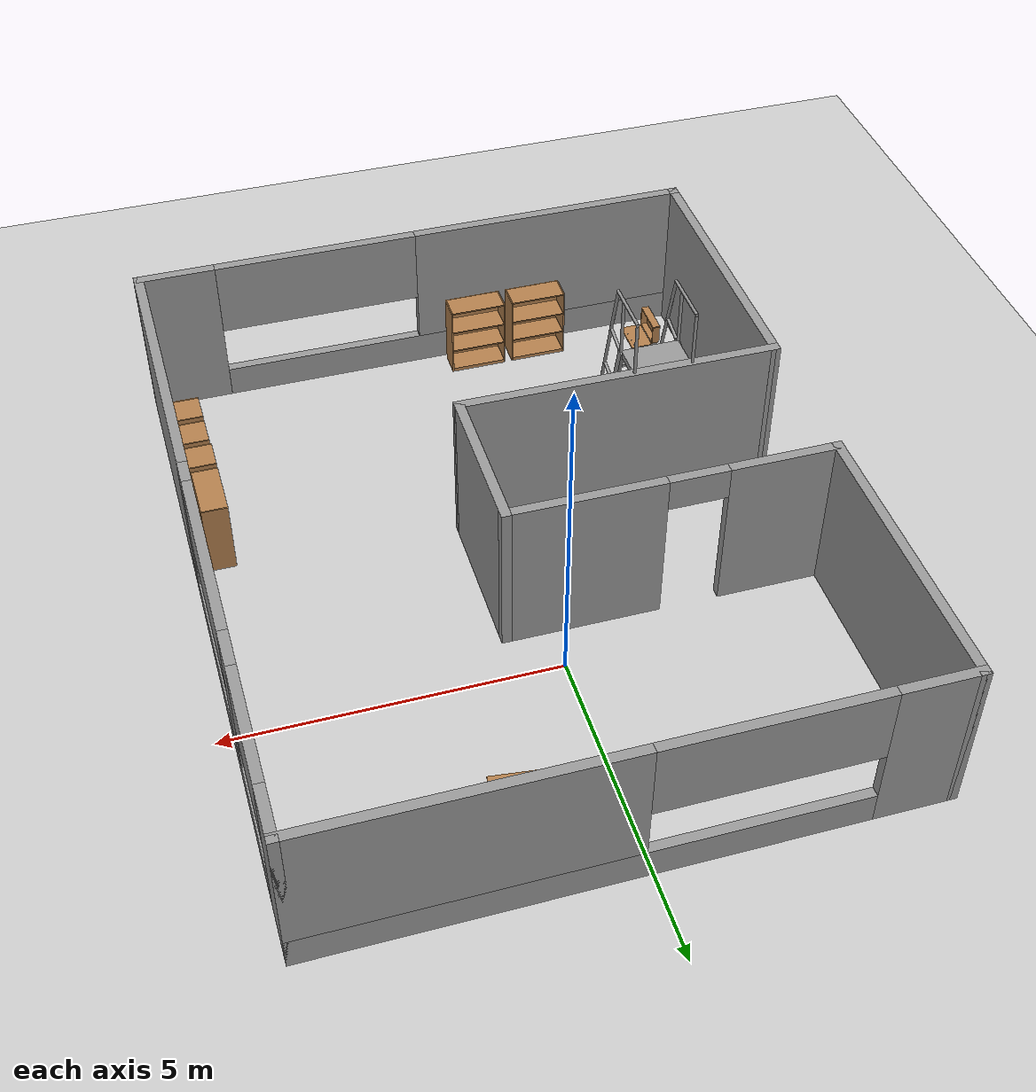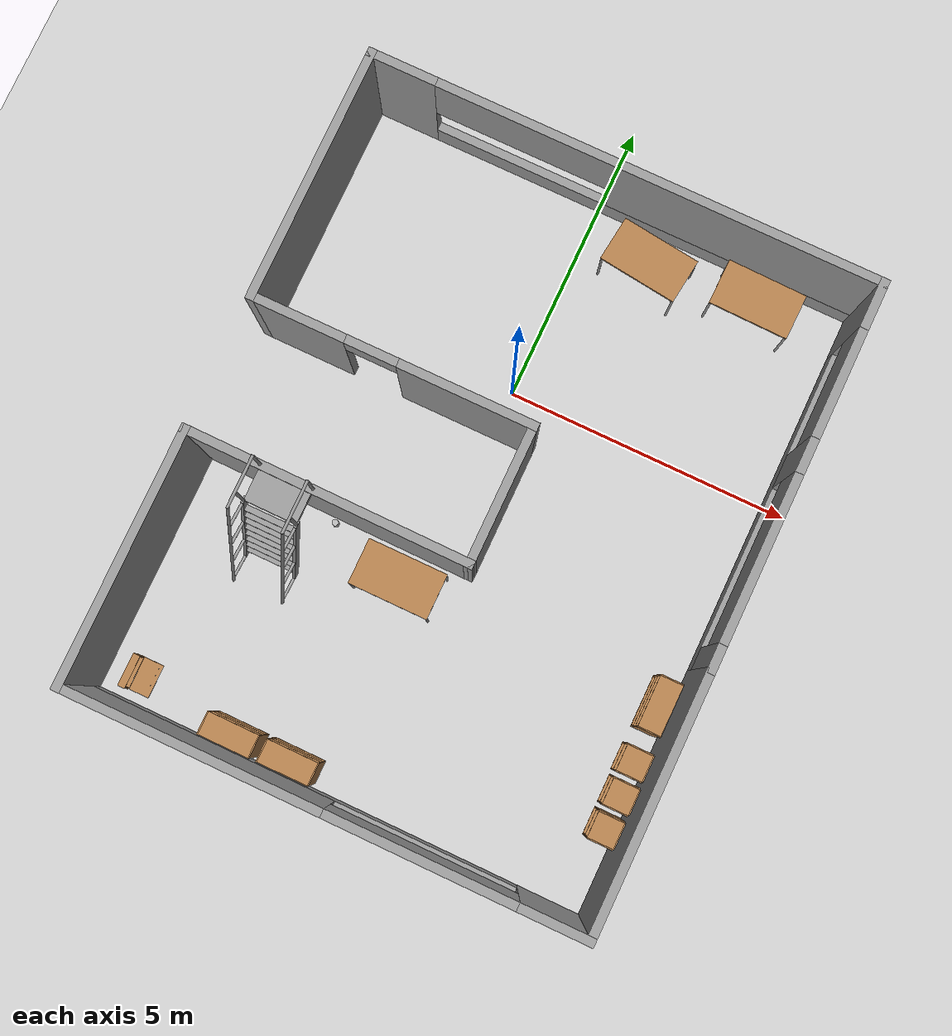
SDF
<sdf version="1.6">
 <world name="default">
  <light name="sun" type="directional">
   <pose>0 0 10 0 -0 0</pose>
   <diffuse>0.8 0.8 0.8 1</diffuse>
   <specular>0.1 0.1 0.1 1</specular>
   <attenuation>
    <range>1000</range>
    <constant>0.9</constant>
    <linear>0.01</linear>
    <quadratic>0.001</quadratic>
   </attenuation>
   <direction>-0.5 0.5 -1</direction>
  </light>
  <model name="ground_plane">
   <static>1</static>
   <link name="link">
    <collision name="collision">
     <geometry><plane><normal>0 0 1</normal><size>100 100</size></plane></geometry>
     <surface><friction><ode><mu>100</mu><mu2>50</mu2></ode></friction></surface>
    </collision>
    <visual name="visual">
     <cast_shadows>0</cast_shadows>
     <geometry><plane><normal>0 0 1</normal><size>100 100</size></plane></geometry>
     <material>
      <script><uri>file://media/materials/scripts/gazebo.material</uri><name>Gazebo/Grey</name></script>
     </material>
    </visual>
   </link>
  </model>
  <gravity>0 0 -9.8</gravity>
  <magnetic_field>6e-06 2.3e-05 -4.2e-05</magnetic_field>
  <atmosphere type="adiabatic"/>
  <physics name="default_physics" default="0" type="ode">
   <max_step_size>0.001</max_step_size>
   <real_time_factor>1</real_time_factor>
   <real_time_update_rate>1000</real_time_update_rate>
  </physics>
  <scene><ambient>0.4 0.4 0.4 1</ambient><background>0.7 0.7 0.7 1</background><shadows>1</shadows></scene>
  <spherical_coordinates>
   <surface_model>EARTH_WGS84</surface_model>
   <latitude_deg>0</latitude_deg>
   <longitude_deg>0</longitude_deg>
   <elevation>0</elevation>
   <heading_deg>0</heading_deg>
  </spherical_coordinates>
  <model name="factory_room">
   <pose>0.23936 -1.91124 0 0 -0 0</pose>
   <link name="Wall_34">
    <collision name="Wall_34_Collision">
     <geometry><box><size>4.5 0.15 2.5</size></box></geometry>
     <pose>0 0 1.25 0 -0 0</pose>
    </collision>
    <visual name="Wall_34_Visual">
     <pose>0 0 1.25 0 -0 0</pose>
     <geometry><box><size>4.5 0.15 2.5</size></box></geometry>
     <material>
      <script><uri>file://media/materials/scripts/gazebo.material</uri><name>Gazebo/Grey</name></script>
      <ambient>1 1 1 1</ambient>
     </material>
    </visual>
    <pose>4.4246 -3.33419 0 0 0 -1.5708</pose>
   </link>
   <link name="Wall_35">
    <pose>-0.0004 -5.50919 0 0 -0 3.14159</pose>
    <visual name="Wall_35_Visual_0">
     <pose>-3.87038 0 1.25 0 -0 0</pose>
     <geometry><box><size>1.25925 0.15 2.5</size></box></geometry>
     <material>
      <script><uri>file://media/materials/scripts/gazebo.material</uri><name>Gazebo/Grey</name></script>
      <ambient>1 1 1 1</ambient>
     </material>
    </visual>
    <collision name="Wall_35_Collision_0">
     <geometry><box><size>1.25925 0.15 2.5</size></box></geometry>
     <pose>-3.87038 0 1.25 0 -0 0</pose>
    </collision>
    <visual name="Wall_35_Visual_1">
     <pose>0.629623 0 0.25 0 -0 0</pose>
     <geometry><box><size>7.74075 0.15 0.5</size></box></geometry>
     <material>
      <script><uri>file://media/materials/scripts/gazebo.material</uri><name>Gazebo/Grey</name></script>
      <ambient>1 1 1 1</ambient>
     </material>
    </visual>
    <collision name="Wall_35_Collision_1">
     <geometry><box><size>7.74075 0.15 0.5</size></box></geometry>
     <pose>0.629623 0 0.25 0 -0 0</pose>
    </collision>
    <visual name="Wall_35_Visual_2">
     <pose>2.24649 0 1.5 0 -0 0</pose>
     <geometry><box><size>4.50701 0.15 2</size></box></geometry>
     <material>
      <script><uri>file://media/materials/scripts/gazebo.material</uri><name>Gazebo/Grey</name></script>
      <ambient>1 1 1 1</ambient>
     </material>
    </visual>
    <collision name="Wall_35_Collision_2">
     <geometry><box><size>4.50701 0.15 2</size></box></geometry>
     <pose>2.24649 0 1.5 0 -0 0</pose>
    </collision>
    <visual name="Wall_35_Visual_3">
     <pose>-1.62388 0 1.9 0 -0 0</pose>
     <geometry><box><size>3.23374 0.15 1.2</size></box></geometry>
     <material>
      <script><uri>file://media/materials/scripts/gazebo.material</uri><name>Gazebo/Grey</name></script>
      <ambient>1 1 1 1</ambient>
     </material>
    </visual>
    <collision name="Wall_35_Collision_3">
     <geometry><box><size>3.23374 0.15 1.2</size></box></geometry>
     <pose>-1.62388 0 1.9 0 -0 0</pose>
    </collision>
   </link>
   <link name="Wall_36">
    <collision name="Wall_36_Collision">
     <geometry><box><size>4.5 0.15 2.5</size></box></geometry>
     <pose>0 0 1.25 0 -0 0</pose>
    </collision>
    <visual name="Wall_36_Visual">
     <pose>0 0 1.25 0 -0 0</pose>
     <geometry><box><size>4.5 0.15 2.5</size></box></geometry>
     <material>
      <script><uri>file://media/materials/scripts/gazebo.material</uri><name>Gazebo/Grey</name></script>
      <ambient>1 1 1 1</ambient>
     </material>
    </visual>
    <pose>-4.4254 -3.33419 0 0 -0 1.5708</pose>
   </link>
   <link name="Wall_38">
    <collision name="Wall_38_Collision">
     <geometry><box><size>2.5 0.15 2.5</size></box></geometry>
     <pose>0 0 1.25 0 -0 0</pose>
    </collision>
    <visual name="Wall_38_Visual">
     <pose>0 0 1.25 0 -0 0</pose>
     <geometry><box><size>2.5 0.15 2.5</size></box></geometry>
     <material>
      <script><uri>file://media/materials/scripts/gazebo.material</uri><name>Gazebo/Grey</name></script>
      <ambient>1 1 1 1</ambient>
     </material>
    </visual>
    <pose>0.425887 -0.015813 0 0 -0 1.5708</pose>
   </link>
   <link name="Wall_39">
    <pose>-1.99911 1.15919 0 0 -0 3.14159</pose>
    <visual name="Wall_39_Visual_0">
     <pose>-1.30008 0 1.25 0 -0 0</pose>
     <geometry><box><size>2.39984 0.15 2.5</size></box></geometry>
     <material>
      <script><uri>file://media/materials/scripts/gazebo.material</uri><name>Gazebo/Grey</name></script>
      <ambient>1 1 1 1</ambient>
     </material>
    </visual>
    <collision name="Wall_39_Collision_0">
     <geometry><box><size>2.39984 0.15 2.5</size></box></geometry>
     <pose>-1.30008 0 1.25 0 -0 0</pose>
    </collision>
    <visual name="Wall_39_Visual_1">
     <pose>1.64992 0 1.25 0 -0 0</pose>
     <geometry><box><size>1.70016 0.15 2.5</size></box></geometry>
     <material>
      <script><uri>file://media/materials/scripts/gazebo.material</uri><name>Gazebo/Grey</name></script>
      <ambient>1 1 1 1</ambient>
     </material>
    </visual>
    <collision name="Wall_39_Collision_1">
     <geometry><box><size>1.70016 0.15 2.5</size></box></geometry>
     <pose>1.64992 0 1.25 0 -0 0</pose>
    </collision>
    <visual name="Wall_39_Visual_2">
     <pose>0.349836 0 2.25 0 -0 0</pose>
     <geometry><box><size>0.9 0.15 0.5</size></box></geometry>
     <material>
      <script><uri>file://media/materials/scripts/gazebo.material</uri><name>Gazebo/Grey</name></script>
      <ambient>1 1 1 1</ambient>
     </material>
    </visual>
    <collision name="Wall_39_Collision_2">
     <geometry><box><size>0.9 0.15 0.5</size></box></geometry>
     <pose>0.349836 0 2.25 0 -0 0</pose>
    </collision>
   </link>
   <link name="Wall_40">
    <collision name="Wall_40_Collision">
     <geometry><box><size>4.5 0.15 2.5</size></box></geometry>
     <pose>0 0 1.25 0 -0 0</pose>
    </collision>
    <visual name="Wall_40_Visual">
     <pose>0 0 1.25 0 -0 0</pose>
     <geometry><box><size>4.5 0.15 2.5</size></box></geometry>
     <material>
      <script><uri>file://media/materials/scripts/gazebo.material</uri><name>Gazebo/Grey</name></script>
      <ambient>1 1 1 1</ambient>
     </material>
    </visual>
    <pose>-4.42411 3.33419 0 0 -0 1.5708</pose>
   </link>
   <link name="Wall_41">
    <pose>0.000887 5.50919 0 0 -0 0</pose>
    <visual name="Wall_41_Visual_0">
     <pose>-3.8901 0 1.25 0 -0 0</pose>
     <geometry><box><size>1.21979 0.15 2.5</size></box></geometry>
     <material>
      <script><uri>file://media/materials/scripts/gazebo.material</uri><name>Gazebo/Grey</name></script>
      <ambient>1 1 1 1</ambient>
     </material>
    </visual>
    <collision name="Wall_41_Collision_0">
     <geometry><box><size>1.21979 0.15 2.5</size></box></geometry>
     <pose>-3.8901 0 1.25 0 -0 0</pose>
    </collision>
    <visual name="Wall_41_Visual_1">
     <pose>0.609898 0 0.25 0 -0 0</pose>
     <geometry><box><size>7.7802 0.15 0.5</size></box></geometry>
     <material>
      <script><uri>file://media/materials/scripts/gazebo.material</uri><name>Gazebo/Grey</name></script>
      <ambient>1 1 1 1</ambient>
     </material>
    </visual>
    <collision name="Wall_41_Collision_1">
     <geometry><box><size>7.7802 0.15 0.5</size></box></geometry>
     <pose>0.609898 0 0.25 0 -0 0</pose>
    </collision>
    <visual name="Wall_41_Visual_2">
     <pose>2.18031 0 1.5 0 -0 0</pose>
     <geometry><box><size>4.63939 0.15 2</size></box></geometry>
     <material>
      <script><uri>file://media/materials/scripts/gazebo.material</uri><name>Gazebo/Grey</name></script>
      <ambient>1 1 1 1</ambient>
     </material>
    </visual>
    <collision name="Wall_41_Collision_2">
     <geometry><box><size>4.63939 0.15 2</size></box></geometry>
     <pose>2.18031 0 1.5 0 -0 0</pose>
    </collision>
    <visual name="Wall_41_Visual_3">
     <pose>-1.7098 0 1.9 0 -0 0</pose>
     <geometry><box><size>3.14082 0.15 1.2</size></box></geometry>
     <material>
      <script><uri>file://media/materials/scripts/gazebo.material</uri><name>Gazebo/Grey</name></script>
      <ambient>1 1 1 1</ambient>
     </material>
    </visual>
    <collision name="Wall_41_Collision_3">
     <geometry><box><size>3.14082 0.15 1.2</size></box></geometry>
     <pose>-1.7098 0 1.9 0 -0 0</pose>
    </collision>
   </link>
   <link name="Wall_42">
    <pose>4.42589 2.20919 0 0 0 -1.5708</pose>
    <visual name="Wall_42_Visual_0">
     <pose>-2.93644 0 1.25 0 -0 0</pose>
     <geometry><box><size>0.87712 0.15 2.5</size></box></geometry>
     <material>
      <script><uri>file://media/materials/scripts/gazebo.material</uri><name>Gazebo/Grey</name></script>
      <ambient>1 1 1 1</ambient>
     </material>
    </visual>
    <collision name="Wall_42_Collision_0">
     <geometry><box><size>0.87712 0.15 2.5</size></box></geometry>
     <pose>-2.93644 0 1.25 0 -0 0</pose>
    </collision>
    <visual name="Wall_42_Visual_1">
     <pose>0.43856 0 0.25 0 -0 0</pose>
     <geometry><box><size>5.87288 0.15 0.5</size></box></geometry>
     <material>
      <script><uri>file://media/materials/scripts/gazebo.material</uri><name>Gazebo/Grey</name></script>
      <ambient>1 1 1 1</ambient>
     </material>
    </visual>
    <collision name="Wall_42_Collision_1">
     <geometry><box><size>5.87288 0.15 0.5</size></box></geometry>
     <pose>0.43856 0 0.25 0 -0 0</pose>
    </collision>
    <visual name="Wall_42_Visual_2">
     <pose>-0.302367 0 1.5 0 -0 0</pose>
     <geometry><box><size>0.609811 0.15 2</size></box></geometry>
     <material>
      <script><uri>file://media/materials/scripts/gazebo.material</uri><name>Gazebo/Grey</name></script>
      <ambient>1 1 1 1</ambient>
     </material>
    </visual>
    <collision name="Wall_42_Collision_2">
     <geometry><box><size>0.609811 0.15 2</size></box></geometry>
     <pose>-0.302367 0 1.5 0 -0 0</pose>
    </collision>
    <visual name="Wall_42_Visual_3">
     <pose>3.13334 0 1.5 0 -0 0</pose>
     <geometry><box><size>0.483315 0.15 2</size></box></geometry>
     <material>
      <script><uri>file://media/materials/scripts/gazebo.material</uri><name>Gazebo/Grey</name></script>
      <ambient>1 1 1 1</ambient>
     </material>
    </visual>
    <collision name="Wall_42_Collision_3">
     <geometry><box><size>0.483315 0.15 2</size></box></geometry>
     <pose>3.13334 0 1.5 0 -0 0</pose>
    </collision>
    <visual name="Wall_42_Visual_4">
     <pose>-1.55258 0 1.9 0 -0 0</pose>
     <geometry><box><size>1.89061 0.15 1.2</size></box></geometry>
     <material>
      <script><uri>file://media/materials/scripts/gazebo.material</uri><name>Gazebo/Grey</name></script>
      <ambient>1 1 1 1</ambient>
     </material>
    </visual>
    <collision name="Wall_42_Collision_4">
     <geometry><box><size>1.89061 0.15 1.2</size></box></geometry>
     <pose>-1.55258 0 1.9 0 -0 0</pose>
    </collision>
    <visual name="Wall_42_Visual_5">
     <pose>1.44711 0 1.9 0 -0 0</pose>
     <geometry><box><size>2.88915 0.15 1.2</size></box></geometry>
     <material>
      <script><uri>file://media/materials/scripts/gazebo.material</uri><name>Gazebo/Grey</name></script>
      <ambient>1 1 1 1</ambient>
     </material>
    </visual>
    <collision name="Wall_42_Collision_5">
     <geometry><box><size>2.88915 0.15 1.2</size></box></geometry>
     <pose>1.44711 0 1.9 0 -0 0</pose>
    </collision>
   </link>
   <link name="Wall_44">
    <collision name="Wall_44_Collision">
     <geometry><box><size>5.00139 0.15 2.5</size></box></geometry>
     <pose>0 0 1.25 0 -0 0</pose>
    </collision>
    <visual name="Wall_44_Visual">
     <pose>0 0 1.25 0 -0 0</pose>
     <geometry><box><size>5.00139 0.15 2.5</size></box></geometry>
     <material>
      <script><uri>file://media/materials/scripts/gazebo.material</uri><name>Gazebo/Grey</name></script>
      <ambient>1 1 1 1</ambient>
     </material>
    </visual>
    <pose>-1.99976 -1.175 0 0 0 -0.006519</pose>
   </link>
   <static>1</static>
  </model>
  <model name="wooden_case">
   <link name="base">
    <pose>0 0 0.024 0 -0 0</pose>
    <inertial>
     <pose>-0.022184 0 0.171592 0 -0 0</pose>
     <mass>3.96264</mass>
     <inertia>
      <ixx>0.213536</ixx>
      <ixy>0</ixy>
      <ixz>0.000779377</ixz>
      <iyy>0.0708943</iyy>
      <iyz>0</iyz>
      <izz>0.154604</izz>
     </inertia>
    </inertial>
    <collision name="collision_back">
     <pose>-0.053975 0 0.1778 0 -0 0</pose>
     <geometry><box><size>0.01905 0.5461 0.3175</size></box></geometry>
     <surface>
      <contact>
       <poissons_ratio>0.347</poissons_ratio>
       <elastic_modulus>8.8e+09</elastic_modulus>
       <ode><kp>100000</kp><kd>100</kd><max_vel>100</max_vel><min_depth>0.001</min_depth></ode>
      </contact>
      <friction>
       <torsional>
        <coefficient>1</coefficient>
        <use_patch_radius>0</use_patch_radius>
        <surface_radius>0.01</surface_radius>
       </torsional>
      </friction>
     </surface>
    </collision>
    <visual name="visual_back">
     <pose>-0.053975 0 0.1778 0 -0 0</pose>
     <geometry><box><size>0.01905 0.5461 0.3175</size></box></geometry>
     <material>
      <script><uri>file://media/materials/scripts/gazebo.material</uri><name>Gazebo/Wood</name></script>
     </material>
    </visual>
    <collision name="collision_bottom">
     <pose>0 0 0.009525 0 -0 0</pose>
     <geometry><box><size>0.127 0.5842 0.01905</size></box></geometry>
     <surface>
      <contact>
       <poissons_ratio>0.347</poissons_ratio>
       <elastic_modulus>8.8e+09</elastic_modulus>
       <ode><kp>100000</kp><kd>100</kd><max_vel>100</max_vel><min_depth>0.001</min_depth></ode>
      </contact>
      <friction>
       <torsional>
        <coefficient>1</coefficient>
        <use_patch_radius>0</use_patch_radius>
        <surface_radius>0.01</surface_radius>
       </torsional>
      </friction>
     </surface>
    </collision>
    <visual name="visual_bottom">
     <pose>0 0 0.009525 0 -0 0</pose>
     <geometry><box><size>0.127 0.5842 0.01905</size></box></geometry>
     <material>
      <script><uri>file://media/materials/scripts/gazebo.material</uri><name>Gazebo/Wood</name></script>
     </material>
    </visual>
    <collision name="collision_top">
     <pose>0 0 0.346075 0 -0 0</pose>
     <geometry><box><size>0.127 0.5842 0.01905</size></box></geometry>
     <surface>
      <contact>
       <poissons_ratio>0.347</poissons_ratio>
       <elastic_modulus>8.8e+09</elastic_modulus>
       <ode><kp>100000</kp><kd>100</kd><max_vel>100</max_vel><min_depth>0.001</min_depth></ode>
      </contact>
      <friction>
       <torsional>
        <coefficient>1</coefficient>
        <use_patch_radius>0</use_patch_radius>
        <surface_radius>0.01</surface_radius>
       </torsional>
      </friction>
     </surface>
    </collision>
    <visual name="visual_top">
     <pose>0 0 0.346075 0 -0 0</pose>
     <geometry><box><size>0.127 0.5842 0.01905</size></box></geometry>
     <material>
      <script><uri>file://media/materials/scripts/gazebo.material</uri><name>Gazebo/Wood</name></script>
     </material>
    </visual>
    <collision name="collision_left">
     <pose>0 -0.282575 0.1778 0 -0 0</pose>
     <geometry><box><size>0.127 0.01905 0.3175</size></box></geometry>
     <surface>
      <contact>
       <poissons_ratio>0.347</poissons_ratio>
       <elastic_modulus>8.8e+09</elastic_modulus>
       <ode><kp>100000</kp><kd>100</kd><max_vel>100</max_vel><min_depth>0.001</min_depth></ode>
      </contact>
      <friction>
       <torsional>
        <coefficient>1</coefficient>
        <use_patch_radius>0</use_patch_radius>
        <surface_radius>0.01</surface_radius>
       </torsional>
      </friction>
     </surface>
    </collision>
    <visual name="visual_left">
     <pose>0 -0.282575 0.1778 0 -0 0</pose>
     <geometry><box><size>0.127 0.01905 0.3175</size></box></geometry>
     <material>
      <script><uri>file://media/materials/scripts/gazebo.material</uri><name>Gazebo/Wood</name></script>
     </material>
    </visual>
    <collision name="collision_right">
     <pose>0 0.282575 0.1778 0 -0 0</pose>
     <geometry><box><size>0.127 0.01905 0.3175</size></box></geometry>
     <surface>
      <contact>
       <poissons_ratio>0.347</poissons_ratio>
       <elastic_modulus>8.8e+09</elastic_modulus>
       <ode><kp>100000</kp><kd>100</kd><max_vel>100</max_vel><min_depth>0.001</min_depth></ode>
      </contact>
      <friction>
       <torsional>
        <coefficient>1</coefficient>
        <use_patch_radius>0</use_patch_radius>
        <surface_radius>0.01</surface_radius>
       </torsional>
      </friction>
     </surface>
    </collision>
    <visual name="visual_right">
     <pose>0 0.282575 0.1778 0 -0 0</pose>
     <geometry><box><size>0.127 0.01905 0.3175</size></box></geometry>
     <material>
      <script><uri>file://media/materials/scripts/gazebo.material</uri><name>Gazebo/Wood</name></script>
     </material>
    </visual>
    <collision name="collision_block_left">
     <pose>0.0095 -0.2151 -0.012 0 -0 0</pose>
     <geometry><box><size>0.108 0.05 0.024</size></box></geometry>
     <surface>
      <contact>
       <poissons_ratio>0.347</poissons_ratio>
       <elastic_modulus>8.8e+09</elastic_modulus>
       <ode><kp>100000</kp><kd>100</kd><max_vel>100</max_vel><min_depth>0.001</min_depth></ode>
      </contact>
      <friction>
       <torsional>
        <coefficient>1</coefficient>
        <use_patch_radius>0</use_patch_radius>
        <surface_radius>0.01</surface_radius>
       </torsional>
      </friction>
     </surface>
    </collision>
    <visual name="visual_block_left">
     <pose>0.0095 -0.2151 -0.012 0 -0 0</pose>
     <geometry><box><size>0.108 0.05 0.024</size></box></geometry>
     <material>
      <script><uri>file://media/materials/scripts/gazebo.material</uri><name>Gazebo/Wood</name></script>
     </material>
    </visual>
    <collision name="collision_block_right">
     <pose>0.0095 0.2151 -0.012 0 -0 0</pose>
     <geometry><box><size>0.108 0.05 0.024</size></box></geometry>
     <surface>
      <contact>
       <poissons_ratio>0.347</poissons_ratio>
       <elastic_modulus>8.8e+09</elastic_modulus>
       <ode><kp>100000</kp><kd>100</kd><max_vel>100</max_vel><min_depth>0.001</min_depth></ode>
      </contact>
      <friction>
       <torsional>
        <coefficient>1</coefficient>
        <use_patch_radius>0</use_patch_radius>
        <surface_radius>0.01</surface_radius>
       </torsional>
      </friction>
     </surface>
    </collision>
    <visual name="visual_block_right">
     <pose>0.0095 0.2151 -0.012 0 -0 0</pose>
     <geometry><box><size>0.108 0.05 0.024</size></box></geometry>
     <material>
      <script><uri>file://media/materials/scripts/gazebo.material</uri><name>Gazebo/Wood</name></script>
     </material>
    </visual>
   </link>
   <link name="lid">
    <pose>0.243775 0 0.009525 0 -0 0</pose>
    <inertial>
     <mass>1.97874</mass>
     <inertia>
      <ixx>0.0563367</ixx>
      <ixy>0</ixy>
      <ixz>0</ixz>
      <iyy>0.020911</iyy>
      <iyz>0</iyz>
      <izz>0.0771281</izz>
     </inertia>
    </inertial>
    <collision name="collision">
     <geometry><box><size>0.3556 0.5842 0.01905</size></box></geometry>
     <surface>
      <contact>
       <poissons_ratio>0.347</poissons_ratio>
       <elastic_modulus>8.8e+09</elastic_modulus>
       <ode><kp>100000</kp><kd>100</kd><max_vel>100</max_vel><min_depth>0.001</min_depth></ode>
      </contact>
      <friction>
       <torsional>
        <coefficient>1</coefficient>
        <use_patch_radius>0</use_patch_radius>
        <surface_radius>0.01</surface_radius>
       </torsional>
      </friction>
     </surface>
    </collision>
    <visual name="visual">
     <geometry><box><size>0.3556 0.5842 0.01905</size></box></geometry>
     <material>
      <script><uri>file://media/materials/scripts/gazebo.material</uri><name>Gazebo/Wood</name></script>
     </material>
    </visual>
    <visual name="tee_nut_1">
     <pose>0.122 -0.216 0 0 -0 0</pose>
     <geometry><cylinder><radius>0.00635</radius><length>0.0192405</length></cylinder></geometry>
     <material>
      <script><uri>file://media/materials/scripts/gazebo.material</uri><name>Gazebo/Grey</name></script>
     </material>
    </visual>
    <visual name="tee_nut_2">
     <pose>0.122 -0.088 0 0 -0 0</pose>
     <geometry><cylinder><radius>0.00635</radius><length>0.0192405</length></cylinder></geometry>
     <material>
      <script><uri>file://media/materials/scripts/gazebo.material</uri><name>Gazebo/Grey</name></script>
     </material>
    </visual>
    <visual name="tee_nut_3">
     <pose>0.122 0.088 0 0 -0 0</pose>
     <geometry><cylinder><radius>0.00635</radius><length>0.0192405</length></cylinder></geometry>
     <material>
      <script><uri>file://media/materials/scripts/gazebo.material</uri><name>Gazebo/Grey</name></script>
     </material>
    </visual>
    <visual name="tee_nut_4">
     <pose>0.122 0.216 0 0 -0 0</pose>
     <geometry><cylinder><radius>0.00635</radius><length>0.0192405</length></cylinder></geometry>
     <material>
      <script><uri>file://media/materials/scripts/gazebo.material</uri><name>Gazebo/Grey</name></script>
     </material>
    </visual>
   </link>
   <joint name="lid_hinge" type="revolute">
    <pose>-0.1778 0 0.01905 0 -0 0</pose>
    <parent>base</parent>
    <child>lid</child>
    <axis>
     <xyz>0 1 0</xyz>
     <limit><upper>0.523599</upper><lower>-1.5708</lower></limit>
     <use_parent_model_frame>0</use_parent_model_frame>
     <dynamics><spring_reference>0</spring_reference><spring_stiffness>0</spring_stiffness></dynamics>
    </axis>
   </joint>
   <pose>-3.72743 -6.89017 -0.001057 -0 -0.000425 1e-06</pose>
  </model>
  <model name="table">
   <static>0</static>
   <link name="link">
    <collision name="surface">
     <pose>0 0 1 0 -0 0</pose>
     <geometry><box><size>1.5 0.8 0.03</size></box></geometry>
     <surface><friction><ode><mu>0.6</mu><mu2>0.6</mu2></ode></friction></surface>
    </collision>
    <visual name="visual1">
     <pose>0 0 1 0 -0 0</pose>
     <geometry><box><size>1.4 0.8 0.04</size></box></geometry>
     <material>
      <script><uri>file://media/materials/scripts/gazebo.material</uri><name>Gazebo/Wood</name></script>
     </material>
    </visual>
    <collision name="front_left_leg">
     <pose>0.68 0.38 0.5 0 -0 0</pose>
     <geometry><cylinder><radius>0.02</radius><length>1</length></cylinder></geometry>
    </collision>
    <visual name="front_left_leg">
     <pose>0.68 0.38 0.5 0 -0 0</pose>
     <geometry><cylinder><radius>0.02</radius><length>1</length></cylinder></geometry>
     <material>
      <script><uri>file://media/materials/scripts/gazebo.material</uri><name>Gazebo/Grey</name></script>
     </material>
    </visual>
    <collision name="front_right_leg">
     <pose>0.68 -0.38 0.5 0 -0 0</pose>
     <geometry><cylinder><radius>0.02</radius><length>1</length></cylinder></geometry>
    </collision>
    <visual name="front_right_leg">
     <pose>0.68 -0.38 0.5 0 -0 0</pose>
     <geometry><cylinder><radius>0.02</radius><length>1</length></cylinder></geometry>
     <material>
      <script><uri>file://media/materials/scripts/gazebo.material</uri><name>Gazebo/Grey</name></script>
     </material>
    </visual>
    <collision name="back_right_leg">
     <pose>-0.68 -0.38 0.5 0 -0 0</pose>
     <geometry><cylinder><radius>0.02</radius><length>1</length></cylinder></geometry>
    </collision>
    <visual name="back_right_leg">
     <pose>-0.68 -0.38 0.5 0 -0 0</pose>
     <geometry><cylinder><radius>0.02</radius><length>1</length></cylinder></geometry>
     <material>
      <script><uri>file://media/materials/scripts/gazebo.material</uri><name>Gazebo/Grey</name></script>
     </material>
    </visual>
    <collision name="back_left_leg">
     <pose>-0.68 0.38 0.5 0 -0 0</pose>
     <geometry><cylinder><radius>0.02</radius><length>1</length></cylinder></geometry>
    </collision>
    <visual name="back_left_leg">
     <pose>-0.68 0.38 0.5 0 -0 0</pose>
     <geometry><cylinder><radius>0.02</radius><length>1</length></cylinder></geometry>
     <material>
      <script><uri>file://media/materials/scripts/gazebo.material</uri><name>Gazebo/Grey</name></script>
     </material>
    </visual>
    <inertial>
     <inertia><ixx>1</ixx><ixy>0</ixy><ixz>0</ixz><iyy>1</iyy><iyz>0</iyz><izz>1</izz></inertia>
     <mass>1</mass>
    </inertial>
   </link>
   <pose>1.1663 2.81965 0 0 0 -0.122893</pose>
  </model>
  <model name="table_0">
   <static>0</static>
   <link name="link">
    <collision name="surface">
     <pose>0 0 1 0 -0 0</pose>
     <geometry><box><size>1.5 0.8 0.03</size></box></geometry>
     <surface><friction><ode><mu>0.6</mu><mu2>0.6</mu2></ode></friction></surface>
    </collision>
    <visual name="visual1">
     <pose>0 0 1 0 -0 0</pose>
     <geometry><box><size>1.4 0.8 0.04</size></box></geometry>
     <material>
      <script><uri>file://media/materials/scripts/gazebo.material</uri><name>Gazebo/Wood</name></script>
     </material>
    </visual>
    <collision name="front_left_leg">
     <pose>0.68 0.38 0.5 0 -0 0</pose>
     <geometry><cylinder><radius>0.02</radius><length>1</length></cylinder></geometry>
    </collision>
    <visual name="front_left_leg">
     <pose>0.68 0.38 0.5 0 -0 0</pose>
     <geometry><cylinder><radius>0.02</radius><length>1</length></cylinder></geometry>
     <material>
      <script><uri>file://media/materials/scripts/gazebo.material</uri><name>Gazebo/Grey</name></script>
     </material>
    </visual>
    <collision name="front_right_leg">
     <pose>0.68 -0.38 0.5 0 -0 0</pose>
     <geometry><cylinder><radius>0.02</radius><length>1</length></cylinder></geometry>
    </collision>
    <visual name="front_right_leg">
     <pose>0.68 -0.38 0.5 0 -0 0</pose>
     <geometry><cylinder><radius>0.02</radius><length>1</length></cylinder></geometry>
     <material>
      <script><uri>file://media/materials/scripts/gazebo.material</uri><name>Gazebo/Grey</name></script>
     </material>
    </visual>
    <collision name="back_right_leg">
     <pose>-0.68 -0.38 0.5 0 -0 0</pose>
     <geometry><cylinder><radius>0.02</radius><length>1</length></cylinder></geometry>
    </collision>
    <visual name="back_right_leg">
     <pose>-0.68 -0.38 0.5 0 -0 0</pose>
     <geometry><cylinder><radius>0.02</radius><length>1</length></cylinder></geometry>
     <material>
      <script><uri>file://media/materials/scripts/gazebo.material</uri><name>Gazebo/Grey</name></script>
     </material>
    </visual>
    <collision name="back_left_leg">
     <pose>-0.68 0.38 0.5 0 -0 0</pose>
     <geometry><cylinder><radius>0.02</radius><length>1</length></cylinder></geometry>
    </collision>
    <visual name="back_left_leg">
     <pose>-0.68 0.38 0.5 0 -0 0</pose>
     <geometry><cylinder><radius>0.02</radius><length>1</length></cylinder></geometry>
     <material>
      <script><uri>file://media/materials/scripts/gazebo.material</uri><name>Gazebo/Grey</name></script>
     </material>
    </visual>
    <inertial>
     <inertia><ixx>1</ixx><ixy>0</ixy><ixz>0</ixz><iyy>1</iyy><iyz>0</iyz><izz>1</izz></inertia>
     <mass>1</mass>
    </inertial>
   </link>
   <pose>3.06043 2.96984 -2e-06 -0 3e-06 -0.019784</pose>
  </model>
  <model name="ladder_75deg_2rails">
   <static>1</static>
   <link name="step0">
    <pose>0 0.071453 0.266667 0 -0 0</pose>
    <inertial>
     <mass>9.75482</mass>
     <inertia>
      <ixx>0.00957124</ixx>
      <iyy>0.65963</iyy>
      <izz>0.666842</izz>
      <ixy>0</ixy>
      <ixz>0</ixz>
      <iyz>0</iyz>
     </inertia>
    </inertial>
    <collision name="collision"><geometry><box><size>0.9 0.1016 0.0381</size></box></geometry></collision>
    <visual name="visual">
     <geometry><box><size>0.9 0.1016 0.0381</size></box></geometry>
     <material>
      <script><uri>file://media/materials/scripts/gazebo.material</uri><name>Gazebo/Grey</name></script>
     </material>
    </visual>
   </link>
   <link name="step1">
    <pose>0 0.142906 0.533333 0 -0 0</pose>
    <inertial>
     <mass>9.75482</mass>
     <inertia>
      <ixx>0.00957124</ixx>
      <iyy>0.65963</iyy>
      <izz>0.666842</izz>
      <ixy>0</ixy>
      <ixz>0</ixz>
      <iyz>0</iyz>
     </inertia>
    </inertial>
    <collision name="collision"><geometry><box><size>0.9 0.1016 0.0381</size></box></geometry></collision>
    <visual name="visual">
     <geometry><box><size>0.9 0.1016 0.0381</size></box></geometry>
     <material>
      <script><uri>file://media/materials/scripts/gazebo.material</uri><name>Gazebo/Grey</name></script>
     </material>
    </visual>
   </link>
   <link name="step2">
    <pose>0 0.214359 0.8 0 -0 0</pose>
    <inertial>
     <mass>9.75482</mass>
     <inertia>
      <ixx>0.00957124</ixx>
      <iyy>0.65963</iyy>
      <izz>0.666842</izz>
      <ixy>0</ixy>
      <ixz>0</ixz>
      <iyz>0</iyz>
     </inertia>
    </inertial>
    <collision name="collision"><geometry><box><size>0.9 0.1016 0.0381</size></box></geometry></collision>
    <visual name="visual">
     <geometry><box><size>0.9 0.1016 0.0381</size></box></geometry>
     <material>
      <script><uri>file://media/materials/scripts/gazebo.material</uri><name>Gazebo/Grey</name></script>
     </material>
    </visual>
   </link>
   <link name="step3">
    <pose>0 0.285812 1.06667 0 -0 0</pose>
    <inertial>
     <mass>9.75482</mass>
     <inertia>
      <ixx>0.00957124</ixx>
      <iyy>0.65963</iyy>
      <izz>0.666842</izz>
      <ixy>0</ixy>
      <ixz>0</ixz>
      <iyz>0</iyz>
     </inertia>
    </inertial>
    <collision name="collision"><geometry><box><size>0.9 0.1016 0.0381</size></box></geometry></collision>
    <visual name="visual">
     <geometry><box><size>0.9 0.1016 0.0381</size></box></geometry>
     <material>
      <script><uri>file://media/materials/scripts/gazebo.material</uri><name>Gazebo/Grey</name></script>
     </material>
    </visual>
   </link>
   <link name="step4">
    <pose>0 0.357266 1.33333 0 -0 0</pose>
    <inertial>
     <mass>9.75482</mass>
     <inertia>
      <ixx>0.00957124</ixx>
      <iyy>0.65963</iyy>
      <izz>0.666842</izz>
      <ixy>0</ixy>
      <ixz>0</ixz>
      <iyz>0</iyz>
     </inertia>
    </inertial>
    <collision name="collision"><geometry><box><size>0.9 0.1016 0.0381</size></box></geometry></collision>
    <visual name="visual">
     <geometry><box><size>0.9 0.1016 0.0381</size></box></geometry>
     <material>
      <script><uri>file://media/materials/scripts/gazebo.material</uri><name>Gazebo/Grey</name></script>
     </material>
    </visual>
   </link>
   <link name="step5">
    <pose>0 0.428719 1.6 0 -0 0</pose>
    <inertial>
     <mass>9.75482</mass>
     <inertia>
      <ixx>0.00957124</ixx>
      <iyy>0.65963</iyy>
      <izz>0.666842</izz>
      <ixy>0</ixy>
      <ixz>0</ixz>
      <iyz>0</iyz>
     </inertia>
    </inertial>
    <collision name="collision"><geometry><box><size>0.9 0.1016 0.0381</size></box></geometry></collision>
    <visual name="visual">
     <geometry><box><size>0.9 0.1016 0.0381</size></box></geometry>
     <material>
      <script><uri>file://media/materials/scripts/gazebo.material</uri><name>Gazebo/Grey</name></script>
     </material>
    </visual>
   </link>
   <link name="step6">
    <pose>0 0.500172 1.86667 0 -0 0</pose>
    <inertial>
     <mass>9.75482</mass>
     <inertia>
      <ixx>0.00957124</ixx>
      <iyy>0.65963</iyy>
      <izz>0.666842</izz>
      <ixy>0</ixy>
      <ixz>0</ixz>
      <iyz>0</iyz>
     </inertia>
    </inertial>
    <collision name="collision"><geometry><box><size>0.9 0.1016 0.0381</size></box></geometry></collision>
    <visual name="visual">
     <geometry><box><size>0.9 0.1016 0.0381</size></box></geometry>
     <material>
      <script><uri>file://media/materials/scripts/gazebo.material</uri><name>Gazebo/Grey</name></script>
     </material>
    </visual>
   </link>
   <link name="step7">
    <pose>0 0.571625 2.13333 0 -0 0</pose>
    <inertial>
     <mass>9.75482</mass>
     <inertia>
      <ixx>0.00957124</ixx>
      <iyy>0.65963</iyy>
      <izz>0.666842</izz>
      <ixy>0</ixy>
      <ixz>0</ixz>
      <iyz>0</iyz>
     </inertia>
    </inertial>
    <collision name="collision"><geometry><box><size>0.9 0.1016 0.0381</size></box></geometry></collision>
    <visual name="visual">
     <geometry><box><size>0.9 0.1016 0.0381</size></box></geometry>
     <material>
      <script><uri>file://media/materials/scripts/gazebo.material</uri><name>Gazebo/Grey</name></script>
     </material>
    </visual>
   </link>
   <link name="landing">
    <pose>0 0.943078 2.4 0 -0 0</pose>
    <inertial>
     <mass>57.6072</mass>
     <inertia><ixx>1.73518</ixx><iyy>3.89545</iyy><izz>5.6167</izz><ixy>0</ixy><ixz>0</ixz><iyz>0</iyz></inertia>
    </inertial>
    <collision name="collision"><geometry><box><size>0.9 0.6 0.1016</size></box></geometry></collision>
    <visual name="visual">
     <geometry><box><size>0.9 0.6 0.1016</size></box></geometry>
     <material>
      <script><uri>file://media/materials/scripts/gazebo.material</uri><name>Gazebo/Grey</name></script>
     </material>
    </visual>
   </link>
   <link name="left_side_wall">
    <pose>-0.45 0.321539 1.2 1.309 -0 0</pose>
    <collision name="collision"><geometry><box><size>0.0508 2.56466 0.13</size></box></geometry></collision>
    <visual name="visual">
     <geometry><box><size>0.0508 2.56466 0.13</size></box></geometry>
     <material>
      <script><uri>file://media/materials/scripts/gazebo.material</uri><name>Gazebo/Grey</name></script>
     </material>
    </visual>
   </link>
   <link name="right_side_wall">
    <pose>0.45 0.321539 1.2 1.309 -0 0</pose>
    <collision name="collision"><geometry><box><size>0.0508 2.56466 0.13</size></box></geometry></collision>
    <visual name="visual">
     <geometry><box><size>0.0508 2.56466 0.13</size></box></geometry>
     <material>
      <script><uri>file://media/materials/scripts/gazebo.material</uri><name>Gazebo/Grey</name></script>
     </material>
    </visual>
   </link>
   <link name="left_railing_long">
    <pose>-0.45 -0.053461 1.66651 -0.261799 0 0</pose>
    <collision name="collision">
     <geometry><cylinder><radius>0.02413</radius><length>3.51529</length></cylinder></geometry>
    </collision>
    <visual name="visual">
     <geometry><cylinder><radius>0.02413</radius><length>3.51529</length></cylinder></geometry>
     <material>
      <script><uri>file://media/materials/scripts/gazebo.material</uri><name>Gazebo/Grey</name></script>
     </material>
    </visual>
   </link>
   <link name="left_railing_upright0">
    <pose>-0.45 -0.210089 0.056293 1.309 -0 0</pose>
    <collision name="collision">
     <geometry><cylinder><radius>0.02413</radius><length>0.482963</length></cylinder></geometry>
    </collision>
    <visual name="visual">
     <geometry><cylinder><radius>0.02413</radius><length>0.482963</length></cylinder></geometry>
     <material>
      <script><uri>file://media/materials/scripts/gazebo.material</uri><name>Gazebo/Grey</name></script>
     </material>
    </visual>
   </link>
   <link name="left_railing_upright1">
    <pose>-0.45 0.00427 0.856293 1.309 -0 0</pose>
    <collision name="collision">
     <geometry><cylinder><radius>0.02413</radius><length>0.482963</length></cylinder></geometry>
    </collision>
    <visual name="visual">
     <geometry><cylinder><radius>0.02413</radius><length>0.482963</length></cylinder></geometry>
     <material>
      <script><uri>file://media/materials/scripts/gazebo.material</uri><name>Gazebo/Grey</name></script>
     </material>
    </visual>
   </link>
   <link name="left_railing_upright2">
    <pose>-0.45 0.21863 1.65629 1.309 -0 0</pose>
    <collision name="collision">
     <geometry><cylinder><radius>0.02413</radius><length>0.482963</length></cylinder></geometry>
    </collision>
    <visual name="visual">
     <geometry><cylinder><radius>0.02413</radius><length>0.482963</length></cylinder></geometry>
     <material>
      <script><uri>file://media/materials/scripts/gazebo.material</uri><name>Gazebo/Grey</name></script>
     </material>
    </visual>
   </link>
   <link name="left_railing_upright3">
    <pose>-0.45 0.432989 2.45629 1.309 -0 0</pose>
    <collision name="collision">
     <geometry><cylinder><radius>0.02413</radius><length>0.482963</length></cylinder></geometry>
    </collision>
    <visual name="visual">
     <geometry><cylinder><radius>0.02413</radius><length>0.482963</length></cylinder></geometry>
     <material>
      <script><uri>file://media/materials/scripts/gazebo.material</uri><name>Gazebo/Grey</name></script>
     </material>
    </visual>
   </link>
   <link name="left_railing_landing_top">
    <pose>-0.45 0.818078 3.35714 1.5708 -0 0</pose>
    <collision name="collision">
     <geometry><cylinder><radius>0.02413</radius><length>0.87413</length></cylinder></geometry>
    </collision>
    <visual name="visual">
     <geometry><cylinder><radius>0.02413</radius><length>0.87413</length></cylinder></geometry>
     <material>
      <script><uri>file://media/materials/scripts/gazebo.material</uri><name>Gazebo/Grey</name></script>
     </material>
    </visual>
   </link>
   <link name="left_railing_landing_upright_0">
    <pose>-0.45 0.643078 2.86651 0 -0 0</pose>
    <collision name="collision">
     <geometry><cylinder><radius>0.02413</radius><length>0.933013</length></cylinder></geometry>
    </collision>
    <visual name="visual">
     <geometry><cylinder><radius>0.02413</radius><length>0.933013</length></cylinder></geometry>
     <material>
      <script><uri>file://media/materials/scripts/gazebo.material</uri><name>Gazebo/Grey</name></script>
     </material>
    </visual>
   </link>
   <link name="left_railing_landing_upright_1">
    <pose>-0.45 1.24308 2.86651 0 -0 0</pose>
    <collision name="collision">
     <geometry><cylinder><radius>0.02413</radius><length>0.933013</length></cylinder></geometry>
    </collision>
    <visual name="visual">
     <geometry><cylinder><radius>0.02413</radius><length>0.933013</length></cylinder></geometry>
     <material>
      <script><uri>file://media/materials/scripts/gazebo.material</uri><name>Gazebo/Grey</name></script>
     </material>
    </visual>
   </link>
   <link name="right_railing_long">
    <pose>0.45 -0.053461 1.66651 -0.261799 0 0</pose>
    <collision name="collision">
     <geometry><cylinder><radius>0.02413</radius><length>3.51529</length></cylinder></geometry>
    </collision>
    <visual name="visual">
     <geometry><cylinder><radius>0.02413</radius><length>3.51529</length></cylinder></geometry>
     <material>
      <script><uri>file://media/materials/scripts/gazebo.material</uri><name>Gazebo/Grey</name></script>
     </material>
    </visual>
   </link>
   <link name="right_railing_upright0">
    <pose>0.45 -0.210089 0.056293 1.309 -0 0</pose>
    <collision name="collision">
     <geometry><cylinder><radius>0.02413</radius><length>0.482963</length></cylinder></geometry>
    </collision>
    <visual name="visual">
     <geometry><cylinder><radius>0.02413</radius><length>0.482963</length></cylinder></geometry>
     <material>
      <script><uri>file://media/materials/scripts/gazebo.material</uri><name>Gazebo/Grey</name></script>
     </material>
    </visual>
   </link>
   <link name="right_railing_upright1">
    <pose>0.45 0.00427 0.856293 1.309 -0 0</pose>
    <collision name="collision">
     <geometry><cylinder><radius>0.02413</radius><length>0.482963</length></cylinder></geometry>
    </collision>
    <visual name="visual">
     <geometry><cylinder><radius>0.02413</radius><length>0.482963</length></cylinder></geometry>
     <material>
      <script><uri>file://media/materials/scripts/gazebo.material</uri><name>Gazebo/Grey</name></script>
     </material>
    </visual>
   </link>
   <link name="right_railing_upright2">
    <pose>0.45 0.21863 1.65629 1.309 -0 0</pose>
    <collision name="collision">
     <geometry><cylinder><radius>0.02413</radius><length>0.482963</length></cylinder></geometry>
    </collision>
    <visual name="visual">
     <geometry><cylinder><radius>0.02413</radius><length>0.482963</length></cylinder></geometry>
     <material>
      <script><uri>file://media/materials/scripts/gazebo.material</uri><name>Gazebo/Grey</name></script>
     </material>
    </visual>
   </link>
   <link name="right_railing_upright3">
    <pose>0.45 0.432989 2.45629 1.309 -0 0</pose>
    <collision name="collision">
     <geometry><cylinder><radius>0.02413</radius><length>0.482963</length></cylinder></geometry>
    </collision>
    <visual name="visual">
     <geometry><cylinder><radius>0.02413</radius><length>0.482963</length></cylinder></geometry>
     <material>
      <script><uri>file://media/materials/scripts/gazebo.material</uri><name>Gazebo/Grey</name></script>
     </material>
    </visual>
   </link>
   <link name="right_railing_landing_top">
    <pose>0.45 0.818078 3.35714 1.5708 -0 0</pose>
    <collision name="collision">
     <geometry><cylinder><radius>0.02413</radius><length>0.87413</length></cylinder></geometry>
    </collision>
    <visual name="visual">
     <geometry><cylinder><radius>0.02413</radius><length>0.87413</length></cylinder></geometry>
     <material>
      <script><uri>file://media/materials/scripts/gazebo.material</uri><name>Gazebo/Grey</name></script>
     </material>
    </visual>
   </link>
   <link name="right_railing_landing_upright_0">
    <pose>0.45 0.643078 2.86651 0 -0 0</pose>
    <collision name="collision">
     <geometry><cylinder><radius>0.02413</radius><length>0.933013</length></cylinder></geometry>
    </collision>
    <visual name="visual">
     <geometry><cylinder><radius>0.02413</radius><length>0.933013</length></cylinder></geometry>
     <material>
      <script><uri>file://media/materials/scripts/gazebo.material</uri><name>Gazebo/Grey</name></script>
     </material>
    </visual>
   </link>
   <link name="right_railing_landing_upright_1">
    <pose>0.45 1.24308 2.86651 0 -0 0</pose>
    <collision name="collision">
     <geometry><cylinder><radius>0.02413</radius><length>0.933013</length></cylinder></geometry>
    </collision>
    <visual name="visual">
     <geometry><cylinder><radius>0.02413</radius><length>0.933013</length></cylinder></geometry>
     <material>
      <script><uri>file://media/materials/scripts/gazebo.material</uri><name>Gazebo/Grey</name></script>
     </material>
    </visual>
   </link>
   <pose>-2.43846 -4.32144 0 0 -0 0</pose>
  </model>
  <model name="wooden_case_metal_peg">
   <link name="wooden_case::base">
    <pose>0 0 0.024 0 -0 0</pose>
    <inertial>
     <pose>-0.022184 0 0.171592 0 -0 0</pose>
     <mass>3.96264</mass>
     <inertia>
      <ixx>0.213536</ixx>
      <ixy>0</ixy>
      <ixz>0.000779377</ixz>
      <iyy>0.0708943</iyy>
      <iyz>0</iyz>
      <izz>0.154604</izz>
     </inertia>
    </inertial>
    <collision name="collision_back">
     <pose>-0.053975 0 0.1778 0 -0 0</pose>
     <geometry><box><size>0.01905 0.5461 0.3175</size></box></geometry>
     <surface>
      <contact>
       <poissons_ratio>0.347</poissons_ratio>
       <elastic_modulus>8.8e+09</elastic_modulus>
       <ode><kp>100000</kp><kd>100</kd><max_vel>100</max_vel><min_depth>0.001</min_depth></ode>
      </contact>
      <friction>
       <torsional>
        <coefficient>1</coefficient>
        <use_patch_radius>0</use_patch_radius>
        <surface_radius>0.01</surface_radius>
       </torsional>
      </friction>
     </surface>
    </collision>
    <visual name="visual_back">
     <pose>-0.053975 0 0.1778 0 -0 0</pose>
     <geometry><box><size>0.01905 0.5461 0.3175</size></box></geometry>
     <material>
      <script><uri>file://media/materials/scripts/gazebo.material</uri><name>Gazebo/Wood</name></script>
     </material>
    </visual>
    <collision name="collision_bottom">
     <pose>0 0 0.009525 0 -0 0</pose>
     <geometry><box><size>0.127 0.5842 0.01905</size></box></geometry>
     <surface>
      <contact>
       <poissons_ratio>0.347</poissons_ratio>
       <elastic_modulus>8.8e+09</elastic_modulus>
       <ode><kp>100000</kp><kd>100</kd><max_vel>100</max_vel><min_depth>0.001</min_depth></ode>
      </contact>
      <friction>
       <torsional>
        <coefficient>1</coefficient>
        <use_patch_radius>0</use_patch_radius>
        <surface_radius>0.01</surface_radius>
       </torsional>
      </friction>
     </surface>
    </collision>
    <visual name="visual_bottom">
     <pose>0 0 0.009525 0 -0 0</pose>
     <geometry><box><size>0.127 0.5842 0.01905</size></box></geometry>
     <material>
      <script><uri>file://media/materials/scripts/gazebo.material</uri><name>Gazebo/Wood</name></script>
     </material>
    </visual>
    <collision name="collision_top">
     <pose>0 0 0.346075 0 -0 0</pose>
     <geometry><box><size>0.127 0.5842 0.01905</size></box></geometry>
     <surface>
      <contact>
       <poissons_ratio>0.347</poissons_ratio>
       <elastic_modulus>8.8e+09</elastic_modulus>
       <ode><kp>100000</kp><kd>100</kd><max_vel>100</max_vel><min_depth>0.001</min_depth></ode>
      </contact>
      <friction>
       <torsional>
        <coefficient>1</coefficient>
        <use_patch_radius>0</use_patch_radius>
        <surface_radius>0.01</surface_radius>
       </torsional>
      </friction>
     </surface>
    </collision>
    <visual name="visual_top">
     <pose>0 0 0.346075 0 -0 0</pose>
     <geometry><box><size>0.127 0.5842 0.01905</size></box></geometry>
     <material>
      <script><uri>file://media/materials/scripts/gazebo.material</uri><name>Gazebo/Wood</name></script>
     </material>
    </visual>
    <collision name="collision_left">
     <pose>0 -0.282575 0.1778 0 -0 0</pose>
     <geometry><box><size>0.127 0.01905 0.3175</size></box></geometry>
     <surface>
      <contact>
       <poissons_ratio>0.347</poissons_ratio>
       <elastic_modulus>8.8e+09</elastic_modulus>
       <ode><kp>100000</kp><kd>100</kd><max_vel>100</max_vel><min_depth>0.001</min_depth></ode>
      </contact>
      <friction>
       <torsional>
        <coefficient>1</coefficient>
        <use_patch_radius>0</use_patch_radius>
        <surface_radius>0.01</surface_radius>
       </torsional>
      </friction>
     </surface>
    </collision>
    <visual name="visual_left">
     <pose>0 -0.282575 0.1778 0 -0 0</pose>
     <geometry><box><size>0.127 0.01905 0.3175</size></box></geometry>
     <material>
      <script><uri>file://media/materials/scripts/gazebo.material</uri><name>Gazebo/Wood</name></script>
     </material>
    </visual>
    <collision name="collision_right">
     <pose>0 0.282575 0.1778 0 -0 0</pose>
     <geometry><box><size>0.127 0.01905 0.3175</size></box></geometry>
     <surface>
      <contact>
       <poissons_ratio>0.347</poissons_ratio>
       <elastic_modulus>8.8e+09</elastic_modulus>
       <ode><kp>100000</kp><kd>100</kd><max_vel>100</max_vel><min_depth>0.001</min_depth></ode>
      </contact>
      <friction>
       <torsional>
        <coefficient>1</coefficient>
        <use_patch_radius>0</use_patch_radius>
        <surface_radius>0.01</surface_radius>
       </torsional>
      </friction>
     </surface>
    </collision>
    <visual name="visual_right">
     <pose>0 0.282575 0.1778 0 -0 0</pose>
     <geometry><box><size>0.127 0.01905 0.3175</size></box></geometry>
     <material>
      <script><uri>file://media/materials/scripts/gazebo.material</uri><name>Gazebo/Wood</name></script>
     </material>
    </visual>
    <collision name="collision_block_left">
     <pose>0.0095 -0.2151 -0.012 0 -0 0</pose>
     <geometry><box><size>0.108 0.05 0.024</size></box></geometry>
     <surface>
      <contact>
       <poissons_ratio>0.347</poissons_ratio>
       <elastic_modulus>8.8e+09</elastic_modulus>
       <ode><kp>100000</kp><kd>100</kd><max_vel>100</max_vel><min_depth>0.001</min_depth></ode>
      </contact>
      <friction>
       <torsional>
        <coefficient>1</coefficient>
        <use_patch_radius>0</use_patch_radius>
        <surface_radius>0.01</surface_radius>
       </torsional>
      </friction>
     </surface>
    </collision>
    <visual name="visual_block_left">
     <pose>0.0095 -0.2151 -0.012 0 -0 0</pose>
     <geometry><box><size>0.108 0.05 0.024</size></box></geometry>
     <material>
      <script><uri>file://media/materials/scripts/gazebo.material</uri><name>Gazebo/Wood</name></script>
     </material>
    </visual>
    <collision name="collision_block_right">
     <pose>0.0095 0.2151 -0.012 0 -0 0</pose>
     <geometry><box><size>0.108 0.05 0.024</size></box></geometry>
     <surface>
      <contact>
       <poissons_ratio>0.347</poissons_ratio>
       <elastic_modulus>8.8e+09</elastic_modulus>
       <ode><kp>100000</kp><kd>100</kd><max_vel>100</max_vel><min_depth>0.001</min_depth></ode>
      </contact>
      <friction>
       <torsional>
        <coefficient>1</coefficient>
        <use_patch_radius>0</use_patch_radius>
        <surface_radius>0.01</surface_radius>
       </torsional>
      </friction>
     </surface>
    </collision>
    <visual name="visual_block_right">
     <pose>0.0095 0.2151 -0.012 0 -0 0</pose>
     <geometry><box><size>0.108 0.05 0.024</size></box></geometry>
     <material>
      <script><uri>file://media/materials/scripts/gazebo.material</uri><name>Gazebo/Wood</name></script>
     </material>
    </visual>
   </link>
   <link name="wooden_case::lid">
    <pose>0.243775 0 0.009525 0 -0 0</pose>
    <inertial>
     <mass>1.97874</mass>
     <inertia>
      <ixx>0.0563367</ixx>
      <ixy>0</ixy>
      <ixz>0</ixz>
      <iyy>0.020911</iyy>
      <iyz>0</iyz>
      <izz>0.0771281</izz>
     </inertia>
    </inertial>
    <collision name="collision">
     <geometry><box><size>0.3556 0.5842 0.01905</size></box></geometry>
     <surface>
      <contact>
       <poissons_ratio>0.347</poissons_ratio>
       <elastic_modulus>8.8e+09</elastic_modulus>
       <ode><kp>100000</kp><kd>100</kd><max_vel>100</max_vel><min_depth>0.001</min_depth></ode>
      </contact>
      <friction>
       <torsional>
        <coefficient>1</coefficient>
        <use_patch_radius>0</use_patch_radius>
        <surface_radius>0.01</surface_radius>
       </torsional>
      </friction>
     </surface>
    </collision>
    <visual name="visual">
     <geometry><box><size>0.3556 0.5842 0.01905</size></box></geometry>
     <material>
      <script><uri>file://media/materials/scripts/gazebo.material</uri><name>Gazebo/Wood</name></script>
     </material>
    </visual>
    <visual name="tee_nut_1">
     <pose>0.122 -0.216 0 0 -0 0</pose>
     <geometry><cylinder><radius>0.00635</radius><length>0.0192405</length></cylinder></geometry>
     <material>
      <script><uri>file://media/materials/scripts/gazebo.material</uri><name>Gazebo/Grey</name></script>
     </material>
    </visual>
    <visual name="tee_nut_2">
     <pose>0.122 -0.088 0 0 -0 0</pose>
     <geometry><cylinder><radius>0.00635</radius><length>0.0192405</length></cylinder></geometry>
     <material>
      <script><uri>file://media/materials/scripts/gazebo.material</uri><name>Gazebo/Grey</name></script>
     </material>
    </visual>
    <visual name="tee_nut_3">
     <pose>0.122 0.088 0 0 -0 0</pose>
     <geometry><cylinder><radius>0.00635</radius><length>0.0192405</length></cylinder></geometry>
     <material>
      <script><uri>file://media/materials/scripts/gazebo.material</uri><name>Gazebo/Grey</name></script>
     </material>
    </visual>
    <visual name="tee_nut_4">
     <pose>0.122 0.216 0 0 -0 0</pose>
     <geometry><cylinder><radius>0.00635</radius><length>0.0192405</length></cylinder></geometry>
     <material>
      <script><uri>file://media/materials/scripts/gazebo.material</uri><name>Gazebo/Grey</name></script>
     </material>
    </visual>
   </link>
   <joint name="wooden_case::lid_hinge" type="revolute">
    <pose>-0.1778 0 0.01905 0 -0 0</pose>
    <parent>wooden_case::base</parent>
    <child>wooden_case::lid</child>
    <axis>
     <xyz>0 1 0</xyz>
     <limit><upper>0.523599</upper><lower>-1.5708</lower></limit>
     <use_parent_model_frame>0</use_parent_model_frame>
     <dynamics><spring_reference>0</spring_reference><spring_stiffness>0</spring_stiffness></dynamics>
    </axis>
   </joint>
   <link name="peg::link">
    <pose>0.365774 0.216 0.05005 0 -0 0</pose>
    <inertial>
     <mass>0.0121</mass>
     <inertia>
      <ixx>3.90898e-06</ixx>
      <ixy>0</ixy>
      <ixz>0</ixz>
      <iyy>3.90898e-06</iyy>
      <iyz>0</iyz>
      <izz>6.58845e-08</izz>
     </inertia>
    </inertial>
    <collision name="collision">
     <geometry><cylinder><radius>0.0033</radius><length>0.062</length></cylinder></geometry>
     <surface>
      <contact>
       <poissons_ratio>0.305</poissons_ratio>
       <elastic_modulus>2e+11</elastic_modulus>
       <ode><kp>100000</kp><kd>100</kd><max_vel>100</max_vel><min_depth>0.001</min_depth></ode>
      </contact>
      <friction>
       <torsional>
        <coefficient>1</coefficient>
        <use_patch_radius>0</use_patch_radius>
        <surface_radius>0.01</surface_radius>
       </torsional>
      </friction>
     </surface>
    </collision>
    <visual name="visual">
     <geometry><cylinder><radius>0.0033</radius><length>0.062</length></cylinder></geometry>
     <material>
      <script><uri>file://media/materials/scripts/gazebo.material</uri><name>Gazebo/Grey</name></script>
     </material>
    </visual>
   </link>
   <joint name="case_peg" type="revolute">
    <child>peg::link</child>
    <parent>wooden_case::lid</parent>
    <axis>
     <xyz>0 0 1</xyz>
     <limit><upper>0</upper><lower>0</lower></limit>
     <use_parent_model_frame>0</use_parent_model_frame>
     <dynamics><spring_reference>0</spring_reference><spring_stiffness>0</spring_stiffness></dynamics>
    </axis>
   </joint>
   <pose>1.19915 3.2886 -0.001057 0 -0.000438 -1.52739</pose>
  </model>
  <model name="wood_cube_10cm">
   <link name="link">
    <pose>0 0 0.05 0 -0 0</pose>
    <inertial>
     <mass>0.5167</mass>
     <inertia>
      <ixx>0.000861167</ixx>
      <ixy>0</ixy>
      <ixz>0</ixz>
      <iyy>0.000861167</iyy>
      <iyz>0</iyz>
      <izz>0.000861167</izz>
     </inertia>
    </inertial>
    <collision name="collision">
     <geometry><box><size>0.1 0.1 0.1</size></box></geometry>
     <surface>
      <contact>
       <poissons_ratio>0.347</poissons_ratio>
       <elastic_modulus>8.8e+09</elastic_modulus>
       <ode><kp>100000</kp><kd>100</kd><max_vel>100</max_vel><min_depth>0.001</min_depth></ode>
      </contact>
      <friction>
       <torsional>
        <coefficient>1</coefficient>
        <use_patch_radius>0</use_patch_radius>
        <surface_radius>0.01</surface_radius>
       </torsional>
      </friction>
     </surface>
    </collision>
    <visual name="visual">
     <geometry><box><size>0.1 0.1 0.1</size></box></geometry>
     <material>
      <script><uri>file://media/materials/scripts/gazebo.material</uri><name>Gazebo/Wood</name></script>
     </material>
    </visual>
   </link>
   <pose>1.67422 3.21228 -0.001013 0 -0 0</pose>
  </model>
  <model name="cabinet">
   <static>1</static>
   <link name="cabinet_bottom_plate">
    <inertial>
     <pose>0 0 -1 0 -0 0</pose>
     <inertia><ixx>2.05</ixx><ixy>0</ixy><ixz>0</ixz><iyy>2.05</iyy><iyz>0</iyz><izz>2.05</izz></inertia>
     <mass>25</mass>
    </inertial>
    <collision name="cabinet_bottom_plate_geom">
     <pose>0 0 0.01 0 -0 0</pose>
     <geometry><box><size>0.45 0.45 0.02</size></box></geometry>
    </collision>
    <visual name="cabinet_bottom_plate_geom_visual">
     <pose>0 0 0.01 0 -0 0</pose>
     <geometry><box><size>0.45 0.45 0.02</size></box></geometry>
     <material>
      <script><uri>file://media/materials/scripts/gazebo.material</uri><name>Gazebo/Wood</name></script>
     </material>
    </visual>
    <collision name="cabinet_bottom_plate_geom_cabinet_back_plate">
     <pose>0.235 0 0.51 0 -0 0</pose>
     <geometry><box><size>0.02 0.45 1.02</size></box></geometry>
    </collision>
    <visual name="cabinet_bottom_plate_geom_cabinet_back_plate_visual">
     <pose>0.235 0 0.51 0 -0 0</pose>
     <geometry><box><size>0.02 0.45 1.02</size></box></geometry>
     <material>
      <script><uri>file://media/materials/scripts/gazebo.material</uri><name>Gazebo/Wood</name></script>
     </material>
    </visual>
    <collision name="cabinet_bottom_plate_geom_cabinet_left_plate">
     <pose>0 0.235 0.51 0 -0 0</pose>
     <geometry><box><size>0.45 0.02 1.02</size></box></geometry>
    </collision>
    <visual name="cabinet_bottom_plate_geom_cabinet_left_plate_visual">
     <pose>0 0.235 0.51 0 -0 0</pose>
     <geometry><box><size>0.45 0.02 1.02</size></box></geometry>
     <material>
      <script><uri>file://media/materials/scripts/gazebo.material</uri><name>Gazebo/Wood</name></script>
     </material>
    </visual>
    <collision name="cabinet_bottom_plate_geom_cabinet_middle_plate">
     <pose>0 0 0.51 0 -0 0</pose>
     <geometry><box><size>0.45 0.45 0.02</size></box></geometry>
    </collision>
    <visual name="cabinet_bottom_plate_geom_cabinet_middle_plate_visual">
     <pose>0 0 0.51 0 -0 0</pose>
     <geometry><box><size>0.45 0.45 0.02</size></box></geometry>
     <material>
      <script><uri>file://media/materials/scripts/gazebo.material</uri><name>Gazebo/Wood</name></script>
     </material>
    </visual>
    <collision name="cabinet_bottom_plate_geom_cabinet_right_plate">
     <pose>0 -0.235 0.51 0 -0 0</pose>
     <geometry><box><size>0.45 0.02 1.02</size></box></geometry>
    </collision>
    <visual name="cabinet_bottom_plate_geom_cabinet_right_plate_visual">
     <pose>0 -0.235 0.51 0 -0 0</pose>
     <geometry><box><size>0.45 0.02 1.02</size></box></geometry>
     <material>
      <script><uri>file://media/materials/scripts/gazebo.material</uri><name>Gazebo/Wood</name></script>
     </material>
    </visual>
    <collision name="cabinet_bottom_plate_geom_cabinet_top_plate">
     <pose>0 0 1.01 0 -0 0</pose>
     <geometry><box><size>0.45 0.45 0.02</size></box></geometry>
    </collision>
    <visual name="cabinet_bottom_plate_geom_cabinet_top_plate_visual">
     <pose>0 0 1.01 0 -0 0</pose>
     <geometry><box><size>0.45 0.45 0.02</size></box></geometry>
     <material>
      <script><uri>file://media/materials/scripts/gazebo.material</uri><name>Gazebo/Wood</name></script>
     </material>
    </visual>
   </link>
   <pose>4.34455 -5.9004 0 0 -0 0</pose>
  </model>
  <model name="cabinet_clone">
   <static>1</static>
   <link name="cabinet_bottom_plate">
    <inertial>
     <pose>0 0 -1 0 -0 0</pose>
     <inertia><ixx>2.05</ixx><ixy>0</ixy><ixz>0</ixz><iyy>2.05</iyy><iyz>0</iyz><izz>2.05</izz></inertia>
     <mass>25</mass>
    </inertial>
    <collision name="cabinet_bottom_plate_geom">
     <pose>0 0 0.01 0 -0 0</pose>
     <geometry><box><size>0.45 0.45 0.02</size></box></geometry>
    </collision>
    <visual name="cabinet_bottom_plate_geom_visual">
     <pose>0 0 0.01 0 -0 0</pose>
     <geometry><box><size>0.45 0.45 0.02</size></box></geometry>
     <material>
      <script><uri>file://media/materials/scripts/gazebo.material</uri><name>Gazebo/Wood</name></script>
     </material>
    </visual>
    <collision name="cabinet_bottom_plate_geom_cabinet_back_plate">
     <pose>0.235 0 0.51 0 -0 0</pose>
     <geometry><box><size>0.02 0.45 1.02</size></box></geometry>
    </collision>
    <visual name="cabinet_bottom_plate_geom_cabinet_back_plate_visual">
     <pose>0.235 0 0.51 0 -0 0</pose>
     <geometry><box><size>0.02 0.45 1.02</size></box></geometry>
     <material>
      <script><uri>file://media/materials/scripts/gazebo.material</uri><name>Gazebo/Wood</name></script>
     </material>
    </visual>
    <collision name="cabinet_bottom_plate_geom_cabinet_left_plate">
     <pose>0 0.235 0.51 0 -0 0</pose>
     <geometry><box><size>0.45 0.02 1.02</size></box></geometry>
    </collision>
    <visual name="cabinet_bottom_plate_geom_cabinet_left_plate_visual">
     <pose>0 0.235 0.51 0 -0 0</pose>
     <geometry><box><size>0.45 0.02 1.02</size></box></geometry>
     <material>
      <script><uri>file://media/materials/scripts/gazebo.material</uri><name>Gazebo/Wood</name></script>
     </material>
    </visual>
    <collision name="cabinet_bottom_plate_geom_cabinet_middle_plate">
     <pose>0 0 0.51 0 -0 0</pose>
     <geometry><box><size>0.45 0.45 0.02</size></box></geometry>
    </collision>
    <visual name="cabinet_bottom_plate_geom_cabinet_middle_plate_visual">
     <pose>0 0 0.51 0 -0 0</pose>
     <geometry><box><size>0.45 0.45 0.02</size></box></geometry>
     <material>
      <script><uri>file://media/materials/scripts/gazebo.material</uri><name>Gazebo/Wood</name></script>
     </material>
    </visual>
    <collision name="cabinet_bottom_plate_geom_cabinet_right_plate">
     <pose>0 -0.235 0.51 0 -0 0</pose>
     <geometry><box><size>0.45 0.02 1.02</size></box></geometry>
    </collision>
    <visual name="cabinet_bottom_plate_geom_cabinet_right_plate_visual">
     <pose>0 -0.235 0.51 0 -0 0</pose>
     <geometry><box><size>0.45 0.02 1.02</size></box></geometry>
     <material>
      <script><uri>file://media/materials/scripts/gazebo.material</uri><name>Gazebo/Wood</name></script>
     </material>
    </visual>
    <collision name="cabinet_bottom_plate_geom_cabinet_top_plate">
     <pose>0 0 1.01 0 -0 0</pose>
     <geometry><box><size>0.45 0.45 0.02</size></box></geometry>
    </collision>
    <visual name="cabinet_bottom_plate_geom_cabinet_top_plate_visual">
     <pose>0 0 1.01 0 -0 0</pose>
     <geometry><box><size>0.45 0.45 0.02</size></box></geometry>
     <material>
      <script><uri>file://media/materials/scripts/gazebo.material</uri><name>Gazebo/Wood</name></script>
     </material>
    </visual>
   </link>
   <pose>4.34487 -5.3232 0 0 -0 0</pose>
  </model>
  <model name="cabinet_clone_0">
   <static>1</static>
   <link name="cabinet_bottom_plate">
    <inertial>
     <pose>0 0 -1 0 -0 0</pose>
     <inertia><ixx>2.05</ixx><ixy>0</ixy><ixz>0</ixz><iyy>2.05</iyy><iyz>0</iyz><izz>2.05</izz></inertia>
     <mass>25</mass>
    </inertial>
    <collision name="cabinet_bottom_plate_geom">
     <pose>0 0 0.01 0 -0 0</pose>
     <geometry><box><size>0.45 0.45 0.02</size></box></geometry>
    </collision>
    <visual name="cabinet_bottom_plate_geom_visual">
     <pose>0 0 0.01 0 -0 0</pose>
     <geometry><box><size>0.45 0.45 0.02</size></box></geometry>
     <material>
      <script><uri>file://media/materials/scripts/gazebo.material</uri><name>Gazebo/Wood</name></script>
     </material>
    </visual>
    <collision name="cabinet_bottom_plate_geom_cabinet_back_plate">
     <pose>0.235 0 0.51 0 -0 0</pose>
     <geometry><box><size>0.02 0.45 1.02</size></box></geometry>
    </collision>
    <visual name="cabinet_bottom_plate_geom_cabinet_back_plate_visual">
     <pose>0.235 0 0.51 0 -0 0</pose>
     <geometry><box><size>0.02 0.45 1.02</size></box></geometry>
     <material>
      <script><uri>file://media/materials/scripts/gazebo.material</uri><name>Gazebo/Wood</name></script>
     </material>
    </visual>
    <collision name="cabinet_bottom_plate_geom_cabinet_left_plate">
     <pose>0 0.235 0.51 0 -0 0</pose>
     <geometry><box><size>0.45 0.02 1.02</size></box></geometry>
    </collision>
    <visual name="cabinet_bottom_plate_geom_cabinet_left_plate_visual">
     <pose>0 0.235 0.51 0 -0 0</pose>
     <geometry><box><size>0.45 0.02 1.02</size></box></geometry>
     <material>
      <script><uri>file://media/materials/scripts/gazebo.material</uri><name>Gazebo/Wood</name></script>
     </material>
    </visual>
    <collision name="cabinet_bottom_plate_geom_cabinet_middle_plate">
     <pose>0 0 0.51 0 -0 0</pose>
     <geometry><box><size>0.45 0.45 0.02</size></box></geometry>
    </collision>
    <visual name="cabinet_bottom_plate_geom_cabinet_middle_plate_visual">
     <pose>0 0 0.51 0 -0 0</pose>
     <geometry><box><size>0.45 0.45 0.02</size></box></geometry>
     <material>
      <script><uri>file://media/materials/scripts/gazebo.material</uri><name>Gazebo/Wood</name></script>
     </material>
    </visual>
    <collision name="cabinet_bottom_plate_geom_cabinet_right_plate">
     <pose>0 -0.235 0.51 0 -0 0</pose>
     <geometry><box><size>0.45 0.02 1.02</size></box></geometry>
    </collision>
    <visual name="cabinet_bottom_plate_geom_cabinet_right_plate_visual">
     <pose>0 -0.235 0.51 0 -0 0</pose>
     <geometry><box><size>0.45 0.02 1.02</size></box></geometry>
     <material>
      <script><uri>file://media/materials/scripts/gazebo.material</uri><name>Gazebo/Wood</name></script>
     </material>
    </visual>
    <collision name="cabinet_bottom_plate_geom_cabinet_top_plate">
     <pose>0 0 1.01 0 -0 0</pose>
     <geometry><box><size>0.45 0.45 0.02</size></box></geometry>
    </collision>
    <visual name="cabinet_bottom_plate_geom_cabinet_top_plate_visual">
     <pose>0 0 1.01 0 -0 0</pose>
     <geometry><box><size>0.45 0.45 0.02</size></box></geometry>
     <material>
      <script><uri>file://media/materials/scripts/gazebo.material</uri><name>Gazebo/Wood</name></script>
     </material>
    </visual>
   </link>
   <pose>4.32656 -4.75391 0 0 -0 0</pose>
  </model>
  <model name="bookshelf">
   <static>1</static>
   <link name="link">
    <inertial><mass>1</mass></inertial>
    <collision name="back">
     <pose>0 0.005 0.6 0 -0 0</pose>
     <geometry><box><size>0.9 0.01 1.2</size></box></geometry>
    </collision>
    <visual name="visual1">
     <pose>0 0.005 0.6 0 -0 0</pose>
     <geometry><box><size>0.9 0.01 1.2</size></box></geometry>
     <material>
      <script><uri>file://media/materials/scripts/gazebo.material</uri><name>Gazebo/Wood</name></script>
     </material>
    </visual>
    <collision name="left_side">
     <pose>0.45 -0.195 0.6 0 -0 0</pose>
     <geometry><box><size>0.02 0.4 1.2</size></box></geometry>
    </collision>
    <visual name="visual2">
     <pose>0.45 -0.195 0.6 0 -0 0</pose>
     <geometry><box><size>0.02 0.4 1.2</size></box></geometry>
     <material>
      <script><uri>file://media/materials/scripts/gazebo.material</uri><name>Gazebo/Wood</name></script>
     </material>
    </visual>
    <collision name="right_side">
     <pose>-0.45 -0.195 0.6 0 -0 0</pose>
     <geometry><box><size>0.02 0.4 1.2</size></box></geometry>
    </collision>
    <visual name="visual3">
     <pose>-0.45 -0.195 0.6 0 -0 0</pose>
     <geometry><box><size>0.02 0.4 1.2</size></box></geometry>
     <material>
      <script><uri>file://media/materials/scripts/gazebo.material</uri><name>Gazebo/Wood</name></script>
     </material>
    </visual>
    <collision name="bottom">
     <pose>0 -0.195 0.03 0 -0 0</pose>
     <geometry><box><size>0.88 0.4 0.06</size></box></geometry>
    </collision>
    <visual name="visual4">
     <pose>0 -0.195 0.03 0 -0 0</pose>
     <geometry><box><size>0.88 0.4 0.06</size></box></geometry>
     <material>
      <script><uri>file://media/materials/scripts/gazebo.material</uri><name>Gazebo/Wood</name></script>
     </material>
    </visual>
    <collision name="top">
     <pose>0 -0.195 1.19 0 -0 0</pose>
     <geometry><box><size>0.88 0.4 0.02</size></box></geometry>
    </collision>
    <visual name="visual5">
     <pose>0 -0.195 1.19 0 -0 0</pose>
     <geometry><box><size>0.88 0.4 0.02</size></box></geometry>
     <material>
      <script><uri>file://media/materials/scripts/gazebo.material</uri><name>Gazebo/Wood</name></script>
     </material>
    </visual>
    <collision name="low_shelf">
     <pose>0 -0.195 0.43 0 -0 0</pose>
     <geometry><box><size>0.88 0.4 0.02</size></box></geometry>
    </collision>
    <visual name="visual6">
     <pose>0 -0.195 0.43 0 -0 0</pose>
     <geometry><box><size>0.88 0.4 0.02</size></box></geometry>
     <material>
      <script><uri>file://media/materials/scripts/gazebo.material</uri><name>Gazebo/Wood</name></script>
     </material>
    </visual>
    <collision name="high_shelf">
     <pose>0 -0.195 0.8 0 -0 0</pose>
     <geometry><box><size>0.88 0.4 0.02</size></box></geometry>
    </collision>
    <visual name="visual7">
     <pose>0 -0.195 0.8 0 -0 0</pose>
     <geometry><box><size>0.88 0.4 0.02</size></box></geometry>
     <material>
      <script><uri>file://media/materials/scripts/gazebo.material</uri><name>Gazebo/Wood</name></script>
     </material>
    </visual>
   </link>
   <pose>4.50878 -3.76621 0 0 0 -1.5708</pose>
  </model>
  <model name="bookshelf_0">
   <static>1</static>
   <link name="link">
    <inertial><mass>1</mass></inertial>
    <collision name="back">
     <pose>0 0.005 0.6 0 -0 0</pose>
     <geometry><box><size>0.9 0.01 1.2</size></box></geometry>
    </collision>
    <visual name="visual1">
     <pose>0 0.005 0.6 0 -0 0</pose>
     <geometry><box><size>0.9 0.01 1.2</size></box></geometry>
     <material>
      <script><uri>file://media/materials/scripts/gazebo.material</uri><name>Gazebo/Wood</name></script>
     </material>
    </visual>
    <collision name="left_side">
     <pose>0.45 -0.195 0.6 0 -0 0</pose>
     <geometry><box><size>0.02 0.4 1.2</size></box></geometry>
    </collision>
    <visual name="visual2">
     <pose>0.45 -0.195 0.6 0 -0 0</pose>
     <geometry><box><size>0.02 0.4 1.2</size></box></geometry>
     <material>
      <script><uri>file://media/materials/scripts/gazebo.material</uri><name>Gazebo/Wood</name></script>
     </material>
    </visual>
    <collision name="right_side">
     <pose>-0.45 -0.195 0.6 0 -0 0</pose>
     <geometry><box><size>0.02 0.4 1.2</size></box></geometry>
    </collision>
    <visual name="visual3">
     <pose>-0.45 -0.195 0.6 0 -0 0</pose>
     <geometry><box><size>0.02 0.4 1.2</size></box></geometry>
     <material>
      <script><uri>file://media/materials/scripts/gazebo.material</uri><name>Gazebo/Wood</name></script>
     </material>
    </visual>
    <collision name="bottom">
     <pose>0 -0.195 0.03 0 -0 0</pose>
     <geometry><box><size>0.88 0.4 0.06</size></box></geometry>
    </collision>
    <visual name="visual4">
     <pose>0 -0.195 0.03 0 -0 0</pose>
     <geometry><box><size>0.88 0.4 0.06</size></box></geometry>
     <material>
      <script><uri>file://media/materials/scripts/gazebo.material</uri><name>Gazebo/Wood</name></script>
     </material>
    </visual>
    <collision name="top">
     <pose>0 -0.195 1.19 0 -0 0</pose>
     <geometry><box><size>0.88 0.4 0.02</size></box></geometry>
    </collision>
    <visual name="visual5">
     <pose>0 -0.195 1.19 0 -0 0</pose>
     <geometry><box><size>0.88 0.4 0.02</size></box></geometry>
     <material>
      <script><uri>file://media/materials/scripts/gazebo.material</uri><name>Gazebo/Wood</name></script>
     </material>
    </visual>
    <collision name="low_shelf">
     <pose>0 -0.195 0.43 0 -0 0</pose>
     <geometry><box><size>0.88 0.4 0.02</size></box></geometry>
    </collision>
    <visual name="visual6">
     <pose>0 -0.195 0.43 0 -0 0</pose>
     <geometry><box><size>0.88 0.4 0.02</size></box></geometry>
     <material>
      <script><uri>file://media/materials/scripts/gazebo.material</uri><name>Gazebo/Wood</name></script>
     </material>
    </visual>
    <collision name="high_shelf">
     <pose>0 -0.195 0.8 0 -0 0</pose>
     <geometry><box><size>0.88 0.4 0.02</size></box></geometry>
    </collision>
    <visual name="visual7">
     <pose>0 -0.195 0.8 0 -0 0</pose>
     <geometry><box><size>0.88 0.4 0.02</size></box></geometry>
     <material>
      <script><uri>file://media/materials/scripts/gazebo.material</uri><name>Gazebo/Wood</name></script>
     </material>
    </visual>
   </link>
   <pose>-0.657126 -7.25842 0 0 -0 3.14159</pose>
  </model>
  <model name="bookshelf_0_clone">
   <static>1</static>
   <link name="link">
    <inertial><mass>1</mass></inertial>
    <collision name="back">
     <pose>0 0.005 0.6 0 -0 0</pose>
     <geometry><box><size>0.9 0.01 1.2</size></box></geometry>
    </collision>
    <visual name="visual1">
     <pose>0 0.005 0.6 0 -0 0</pose>
     <geometry><box><size>0.9 0.01 1.2</size></box></geometry>
     <material>
      <script><uri>file://media/materials/scripts/gazebo.material</uri><name>Gazebo/Wood</name></script>
     </material>
    </visual>
    <collision name="left_side">
     <pose>0.45 -0.195 0.6 0 -0 0</pose>
     <geometry><box><size>0.02 0.4 1.2</size></box></geometry>
    </collision>
    <visual name="visual2">
     <pose>0.45 -0.195 0.6 0 -0 0</pose>
     <geometry><box><size>0.02 0.4 1.2</size></box></geometry>
     <material>
      <script><uri>file://media/materials/scripts/gazebo.material</uri><name>Gazebo/Wood</name></script>
     </material>
    </visual>
    <collision name="right_side">
     <pose>-0.45 -0.195 0.6 0 -0 0</pose>
     <geometry><box><size>0.02 0.4 1.2</size></box></geometry>
    </collision>
    <visual name="visual3">
     <pose>-0.45 -0.195 0.6 0 -0 0</pose>
     <geometry><box><size>0.02 0.4 1.2</size></box></geometry>
     <material>
      <script><uri>file://media/materials/scripts/gazebo.material</uri><name>Gazebo/Wood</name></script>
     </material>
    </visual>
    <collision name="bottom">
     <pose>0 -0.195 0.03 0 -0 0</pose>
     <geometry><box><size>0.88 0.4 0.06</size></box></geometry>
    </collision>
    <visual name="visual4">
     <pose>0 -0.195 0.03 0 -0 0</pose>
     <geometry><box><size>0.88 0.4 0.06</size></box></geometry>
     <material>
      <script><uri>file://media/materials/scripts/gazebo.material</uri><name>Gazebo/Wood</name></script>
     </material>
    </visual>
    <collision name="top">
     <pose>0 -0.195 1.19 0 -0 0</pose>
     <geometry><box><size>0.88 0.4 0.02</size></box></geometry>
    </collision>
    <visual name="visual5">
     <pose>0 -0.195 1.19 0 -0 0</pose>
     <geometry><box><size>0.88 0.4 0.02</size></box></geometry>
     <material>
      <script><uri>file://media/materials/scripts/gazebo.material</uri><name>Gazebo/Wood</name></script>
     </material>
    </visual>
    <collision name="low_shelf">
     <pose>0 -0.195 0.43 0 -0 0</pose>
     <geometry><box><size>0.88 0.4 0.02</size></box></geometry>
    </collision>
    <visual name="visual6">
     <pose>0 -0.195 0.43 0 -0 0</pose>
     <geometry><box><size>0.88 0.4 0.02</size></box></geometry>
     <material>
      <script><uri>file://media/materials/scripts/gazebo.material</uri><name>Gazebo/Wood</name></script>
     </material>
    </visual>
    <collision name="high_shelf">
     <pose>0 -0.195 0.8 0 -0 0</pose>
     <geometry><box><size>0.88 0.4 0.02</size></box></geometry>
    </collision>
    <visual name="visual7">
     <pose>0 -0.195 0.8 0 -0 0</pose>
     <geometry><box><size>0.88 0.4 0.02</size></box></geometry>
     <material>
      <script><uri>file://media/materials/scripts/gazebo.material</uri><name>Gazebo/Wood</name></script>
     </material>
    </visual>
   </link>
   <pose>-1.69386 -7.26338 0 0 -0 3.14159</pose>
  </model>
  <model name="beer">
   <link name="link">
    <pose>0 0 0.115 0 -0 0</pose>
    <inertial>
     <mass>0.39</mass>
     <inertia><ixx>0.00058</ixx><ixy>0</ixy><ixz>0</ixz><iyy>0.00058</iyy><iyz>0</iyz><izz>0.00019</izz></inertia>
    </inertial>
    <collision name="collision">
     <geometry><cylinder><radius>0.055</radius><length>0.23</length></cylinder></geometry>
    </collision>
    <visual name="visual">
     <geometry><cylinder><radius>0.055</radius><length>0.23</length></cylinder></geometry>
     <material>
      <script>
       <uri>model://beer/materials/scripts</uri>
       <uri>model://beer/materials/textures</uri>
       <name>Beer/Diffuse</name>
      </script>
     </material>
    </visual>
   </link>
   <pose>-2.49892 -3.64526 -2e-06 1e-06 -0 -1.3e-05</pose>
  </model>
  <model name="beer_0">
   <link name="link">
    <pose>0 0 0.115 0 -0 0</pose>
    <inertial>
     <mass>0.39</mass>
     <inertia><ixx>0.00058</ixx><ixy>0</ixy><ixz>0</ixz><iyy>0.00058</iyy><iyz>0</iyz><izz>0.00019</izz></inertia>
    </inertial>
    <collision name="collision">
     <geometry><cylinder><radius>0.055</radius><length>0.23</length></cylinder></geometry>
    </collision>
    <visual name="visual">
     <geometry><cylinder><radius>0.055</radius><length>0.23</length></cylinder></geometry>
     <material>
      <script>
       <uri>model://beer/materials/scripts</uri>
       <uri>model://beer/materials/textures</uri>
       <name>Beer/Diffuse</name>
      </script>
     </material>
    </visual>
   </link>
   <pose>-1.74107 -3.25339 -7e-06 -1e-06 -0 -1.3e-05</pose>
  </model>
  <model name="table_1">
   <static>0</static>
   <link name="link">
    <collision name="surface">
     <pose>0 0 1 0 -0 0</pose>
     <geometry><box><size>1.5 0.8 0.03</size></box></geometry>
     <surface><friction><ode><mu>0.6</mu><mu2>0.6</mu2></ode></friction></surface>
    </collision>
    <visual name="visual1">
     <pose>0 0 1 0 -0 0</pose>
     <geometry><box><size>1.4 0.8 0.04</size></box></geometry>
     <material>
      <script><uri>file://media/materials/scripts/gazebo.material</uri><name>Gazebo/Wood</name></script>
     </material>
    </visual>
    <collision name="front_left_leg">
     <pose>0.68 0.38 0.5 0 -0 0</pose>
     <geometry><cylinder><radius>0.02</radius><length>1</length></cylinder></geometry>
    </collision>
    <visual name="front_left_leg">
     <pose>0.68 0.38 0.5 0 -0 0</pose>
     <geometry><cylinder><radius>0.02</radius><length>1</length></cylinder></geometry>
     <material>
      <script><uri>file://media/materials/scripts/gazebo.material</uri><name>Gazebo/Grey</name></script>
     </material>
    </visual>
    <collision name="front_right_leg">
     <pose>0.68 -0.38 0.5 0 -0 0</pose>
     <geometry><cylinder><radius>0.02</radius><length>1</length></cylinder></geometry>
    </collision>
    <visual name="front_right_leg">
     <pose>0.68 -0.38 0.5 0 -0 0</pose>
     <geometry><cylinder><radius>0.02</radius><length>1</length></cylinder></geometry>
     <material>
      <script><uri>file://media/materials/scripts/gazebo.material</uri><name>Gazebo/Grey</name></script>
     </material>
    </visual>
    <collision name="back_right_leg">
     <pose>-0.68 -0.38 0.5 0 -0 0</pose>
     <geometry><cylinder><radius>0.02</radius><length>1</length></cylinder></geometry>
    </collision>
    <visual name="back_right_leg">
     <pose>-0.68 -0.38 0.5 0 -0 0</pose>
     <geometry><cylinder><radius>0.02</radius><length>1</length></cylinder></geometry>
     <material>
      <script><uri>file://media/materials/scripts/gazebo.material</uri><name>Gazebo/Grey</name></script>
     </material>
    </visual>
    <collision name="back_left_leg">
     <pose>-0.68 0.38 0.5 0 -0 0</pose>
     <geometry><cylinder><radius>0.02</radius><length>1</length></cylinder></geometry>
    </collision>
    <visual name="back_left_leg">
     <pose>-0.68 0.38 0.5 0 -0 0</pose>
     <geometry><cylinder><radius>0.02</radius><length>1</length></cylinder></geometry>
     <material>
      <script><uri>file://media/materials/scripts/gazebo.material</uri><name>Gazebo/Grey</name></script>
     </material>
    </visual>
    <inertial>
     <inertia><ixx>1</ixx><ixy>0</ixy><ixz>0</ixz><iyy>1</iyy><iyz>0</iyz><izz>1</izz></inertia>
     <mass>1</mass>
    </inertial>
   </link>
   <pose>-0.335042 -3.69989 -9e-06 1e-06 -1e-06 0</pose>
  </model>
  <model name="wood_cube_10cm_0">
   <link name="link">
    <pose>0 0 0.05 0 -0 0</pose>
    <inertial>
     <mass>0.5167</mass>
     <inertia>
      <ixx>0.000861167</ixx>
      <ixy>0</ixy>
      <ixz>0</ixz>
      <iyy>0.000861167</iyy>
      <iyz>0</iyz>
      <izz>0.000861167</izz>
     </inertia>
    </inertial>
    <collision name="collision">
     <geometry><box><size>0.1 0.1 0.1</size></box></geometry>
     <surface>
      <contact>
       <poissons_ratio>0.347</poissons_ratio>
       <elastic_modulus>8.8e+09</elastic_modulus>
       <ode><kp>100000</kp><kd>100</kd><max_vel>100</max_vel><min_depth>0.001</min_depth></ode>
      </contact>
      <friction>
       <torsional>
        <coefficient>1</coefficient>
        <use_patch_radius>0</use_patch_radius>
        <surface_radius>0.01</surface_radius>
       </torsional>
      </friction>
     </surface>
    </collision>
    <visual name="visual">
     <geometry><box><size>0.1 0.1 0.1</size></box></geometry>
     <material>
      <script><uri>file://media/materials/scripts/gazebo.material</uri><name>Gazebo/Wood</name></script>
     </material>
    </visual>
   </link>
   <pose>0.769568 3.04391 -0.001013 0 -0 0</pose>
  </model>
 </world>
</sdf>
